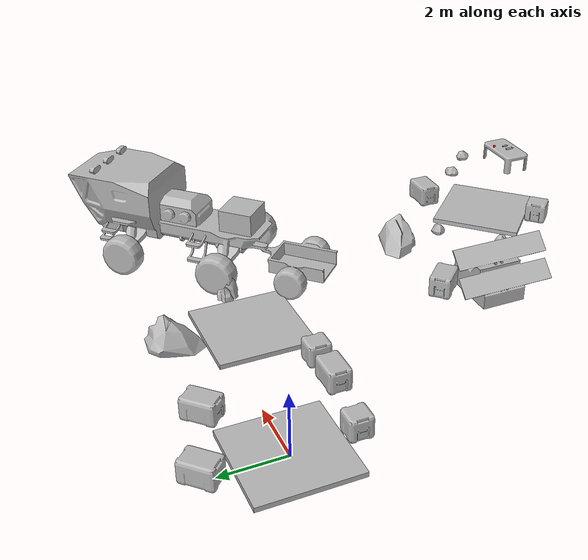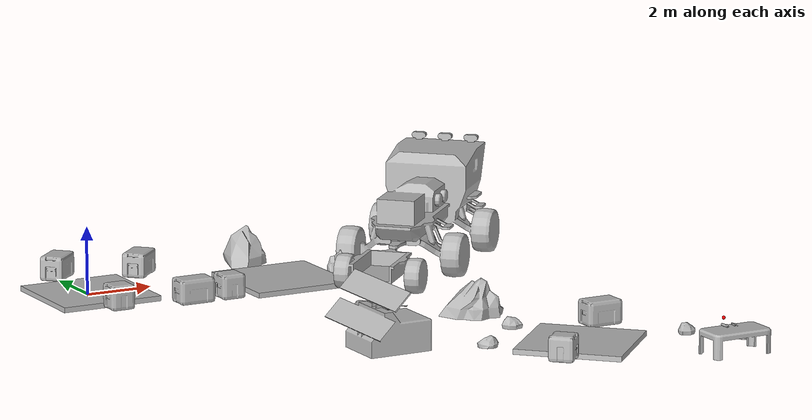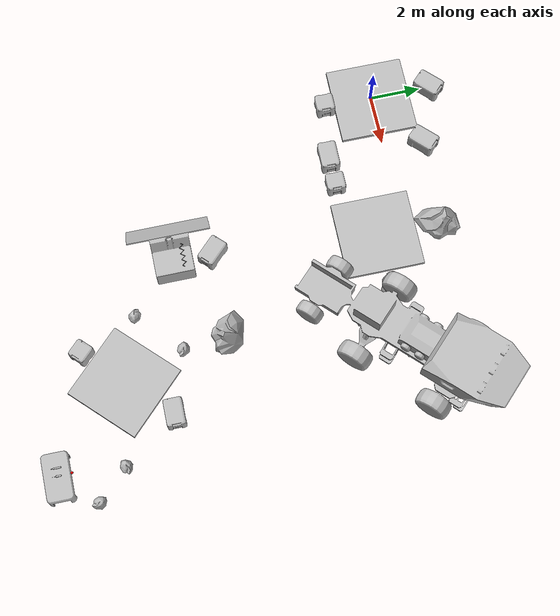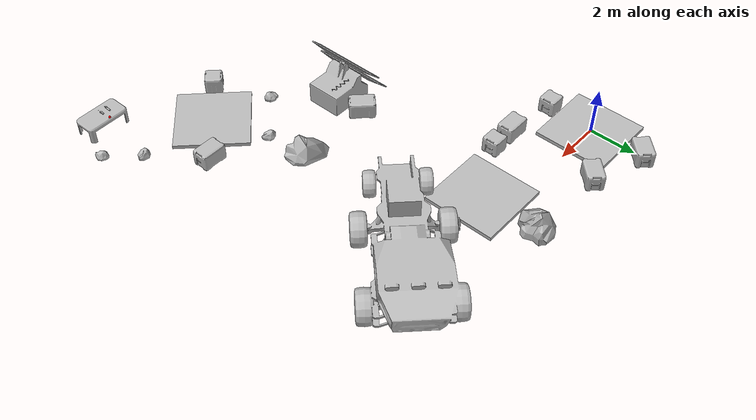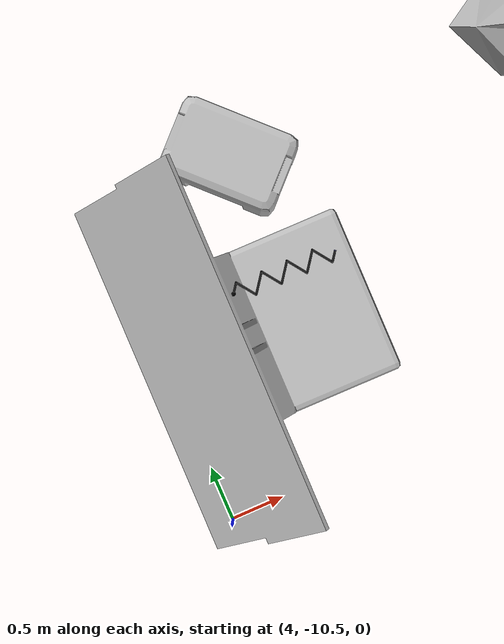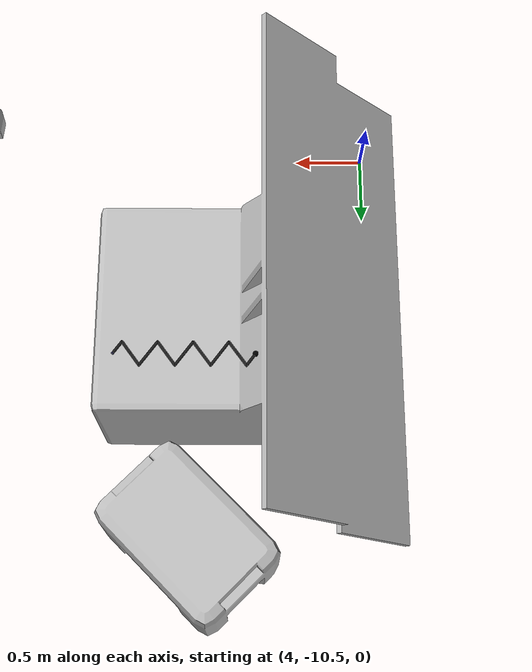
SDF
<sdf version="1.6">
 <world name="SRC_finals">
  <physics type="ode">
   <real_time_update_rate>1000.0</real_time_update_rate>
   <max_step_size>0.001</max_step_size>
   <real_time_factor>1</real_time_factor>
   <ode>
    <solver>
     <type>quick</type>
     <iters>150</iters>
     <precon_iters>0</precon_iters>
     <sor>1.400000</sor>
     <use_dynamic_moi_rescaling>1</use_dynamic_moi_rescaling>
    </solver>
    <constraints>
     <cfm>0.000000</cfm>
     <erp>0.800000</erp>
     <contact_max_correcting_vel>2000.000000</contact_max_correcting_vel>
     <contact_surface_layer>0.01000</contact_surface_layer>
    </constraints>
   </ode>
  </physics>
  <scene>
   <background>0.968627451 0.690196078 0.384313725 1.0</background>
   <grid>0</grid>
   <origin_visual>0</origin_visual>
  </scene>
  <light type="directional" name="sun">
   <pose>0 0 1000 -0.1700415195883993 -1.1783325251044838 0</pose>
   <diffuse>0.8 0.8 0.8 1</diffuse>
   <specular>0.2 0.2 0.2 1</specular>
   <attenuation>
    <range>1000</range>
    <constant>0.9</constant>
    <linear>0.01</linear>
    <quadratic>0.001</quadratic>
   </attenuation>
   <direction>-0.5 0.1 -0.9</direction>
  </light>
  <include>
   <name>walkway_1</name>
   <pose>0.09
      0
      -0.052151
      0
      0
      3.141592653589793</pose>
   <uri>model://walkway_finish_opposite</uri>
  </include>
  <include>
   <name>mars_crate_long_1</name>
   <pose>0.09000000000000037
      2.324
      0
      0
      0
      0.785398163397448</pose>
   <uri>model://mars_crate_long</uri>
  </include>
  <include>
   <name>mars_crate_2</name>
   <pose>0.08999999999999976
      -1.924
      0
      0
      0
      3.141592653589793</pose>
   <uri>model://mars_crate</uri>
  </include>
  <plugin name="boxT1Start" filename="libBoxContainsPlugin.so">
   <entity>valkyrie</entity>
   <namespace>task1/start</namespace>
   <pose>2.114
        -2.784846821261081e-16
        2.5
        0
        0
        -1.5707963267948968</pose>
   <size>1.524 1 5.0</size>
  </plugin>
  <plugin name="boxT1CP1" filename="libBoxContainsPlugin.so">
   <entity>valkyrie</entity>
   <namespace>task1/checkpoint1</namespace>
   <pose>2.687517287525381
        0.3267572875253808
        2.5
        0
        0
        0.7853981633974481</pose>
   <size>1 1 5.0</size>
  </plugin>
  <include>
   <name>mars_crate_long_3</name>
   <pose>2.3760000000000003
      1.5619999999999998
      0
      0
      0
      0.785398163397448</pose>
   <uri>model://mars_crate_long</uri>
  </include>
  <include>
   <name>mars_crate_4</name>
   <pose>3.4539547922204332
      -2.2397649636193724
      0
      0
      0
      3.141592653589793</pose>
   <uri>model://mars_crate</uri>
  </include>
  <include>
   <name>mars_crate_long_5</name>
   <pose>2.293909367271195
      -2.25305038856861
      0
      0
      0
      3.141592653589793</pose>
   <uri>model://mars_crate_long</uri>
  </include>
  <include>
   <name>walkway_4</name>
   <pose>5.739954792220433
      -1.0777649636193727
      -0.052151
      0
      0
      3.141592653589793</pose>
   <uri>model://walkway_finish_adjacent</uri>
  </include>
  <plugin name="boxT1CP3" filename="libBoxContainsPlugin.so">
   <entity>valkyrie</entity>
   <namespace>task1/checkpoint3</namespace>
   <pose>5.739954792220433
        -1.0777649636193727
        2.5
        0
        0
        3.141592653589793</pose>
   <size>3.048 3.048 5.0</size>
  </plugin>
  <include>
   <name>mars_rock_2_6</name>
   <pose>7.763954792220433
      -1.0777649636193727
      0
      0
      0
      -1.5707963267948968</pose>
   <uri>model://mars_rock_2</uri>
  </include>
  <include>
   <name>mars_rock_3_7</name>
   <pose>5.739954792220433
      1.5462350363806274
      0
      0
      0
      -1.8369701987210297e-16</pose>
   <uri>model://mars_rock_3</uri>
  </include>
  <plugin name="boxT2Start" filename="libBoxContainsPlugin.so">
   <entity>valkyrie</entity>
   <namespace>task2/start</namespace>
   <pose>5.739954792220433
        -3.101764963619373
        2.5
        0
        0
        3.141592653589793</pose>
   <size>1.524 1 5.0</size>
  </plugin>
  <include>
   <pose>10.539036134088196
        -0.7205184482799094
        0
        0
        0
        2.356194490192345</pose>
   <uri>model://mars_explorer</uri>
  </include>
  <include>
   <name>mars_crate_long_8</name>
   <pose>5.255719755839805
      -7.489719755839806
      0
      0
      0
      2.356194490192345</pose>
   <uri>model://mars_crate_long</uri>
  </include>
  <include>
   <name>mars_rock_3_9</name>
   <pose>8.679719755839805
      -7.489719755839806
      0
      0
      0
      -1.5707963267948968</pose>
   <uri>model://mars_rock_3</uri>
  </include>
  <include>
   <pose>5.417046200298301
        -9.02441469592094
        0
        0
        0
        1.5707963267948966</pose>
   <uri>model://solar_array</uri>
  </include>
  <model name="solar_panel_cable">
   <self_collide>true</self_collide>
   <pose>4.8170462002983
    -8.62441469592094
    0.85
    0
    0
    6.123233995736766e-17</pose>
   <link name="link_0">
    <inertial><mass>0.05</mass><inertia><ixx>0.0001</ixx><iyy>0.0001</iyy><izz>0.0001</izz></inertia></inertial>
    <visual name="visual">
     <geometry><sphere><radius>0.02</radius></sphere></geometry>
     <material>
      <ambient>0 0 0 1</ambient>
      <emissive>0 0 0 1</emissive>
      <diffuse>0 0 0 1</diffuse>
      <specular>1 1 1 1</specular>
     </material>
    </visual>
   </link>
   <link name="link_1">
    <pose>0.0 0 0 0 1.5707963267948966 0.9424777960769379</pose>
    <inertial>
     <pose>0 0 0.05 0 0 0</pose>
     <mass>0.05</mass>
     <inertia><ixx>0.0001</ixx><iyy>0.0001</iyy><izz>0.0001</izz></inertia>
    </inertial>
    <collision name="cylinder">
     <pose>0 0 0.05 0 0 0</pose>
     <geometry><cylinder><length>0.1</length><radius>0.01</radius></cylinder></geometry>
     <surface>
      <contact><ode><kp>1e5</kp><kd>1</kd><max_vel>0.1</max_vel><min_depth>0.0015</min_depth></ode></contact>
      <friction><ode><mu>1.0</mu><mu2>1.0</mu2></ode></friction>
     </surface>
    </collision>
    <collision name="sphere">
     <geometry><sphere><radius>0.01</radius></sphere></geometry>
     <surface>
      <contact><ode><kp>1e5</kp><kd>1</kd><max_vel>0.1</max_vel><min_depth>0.0015</min_depth></ode></contact>
      <friction><ode><mu>1.0</mu><mu2>1.0</mu2></ode></friction>
     </surface>
    </collision>
    <visual name="cylinder">
     <pose>0 0 0.05 0 0 0</pose>
     <geometry><cylinder><length>0.1</length><radius>0.01</radius></cylinder></geometry>
     <material>
      <ambient>0 0 0 1</ambient>
      <emissive>0 0 0 1</emissive>
      <diffuse>0.1 0.1 0.1 1</diffuse>
      <specular>1 1 1 1</specular>
     </material>
    </visual>
    <visual name="sphere">
     <geometry><sphere><radius>0.01</radius></sphere></geometry>
     <material>
      <ambient>0 0 0 1</ambient>
      <emissive>0 0 0 1</emissive>
      <diffuse>0.1 0.1 0.1 1</diffuse>
      <specular>1 1 1 1</specular>
     </material>
    </visual>
   </link>
   <joint name="joint_1" type="universal">
    <child>link_1</child>
    <parent>link_0</parent>
    <axis>
     <xyz>0 1 0</xyz>
     <limit><lower>-1.5707963267948966</lower><upper>1.5707963267948966</upper></limit>
    </axis>
    <axis2>
     <xyz>-1 0 0</xyz>
     <limit><lower>-1.5707963267948966</lower><upper>1.5707963267948966</upper></limit>
    </axis2>
    <physics><ode><cfm_damping>1</cfm_damping></ode></physics>
   </joint>
   <link name="link_2">
    <pose>0.058778525229247314 0.08090169943749476 0 0 1.5707963267948966 -0.9424777960769379</pose>
    <inertial>
     <pose>0 0 0.05 0 0 0</pose>
     <mass>0.05</mass>
     <inertia><ixx>0.0001</ixx><iyy>0.0001</iyy><izz>0.0001</izz></inertia>
    </inertial>
    <collision name="cylinder">
     <pose>0 0 0.05 0 0 0</pose>
     <geometry><cylinder><length>0.1</length><radius>0.01</radius></cylinder></geometry>
     <surface>
      <contact><ode><kp>1e5</kp><kd>1</kd><max_vel>0.1</max_vel><min_depth>0.0015</min_depth></ode></contact>
      <friction><ode><mu>1.0</mu><mu2>1.0</mu2></ode></friction>
     </surface>
    </collision>
    <collision name="sphere">
     <geometry><sphere><radius>0.01</radius></sphere></geometry>
     <surface>
      <contact><ode><kp>1e5</kp><kd>1</kd><max_vel>0.1</max_vel><min_depth>0.0015</min_depth></ode></contact>
      <friction><ode><mu>1.0</mu><mu2>1.0</mu2></ode></friction>
     </surface>
    </collision>
    <visual name="cylinder">
     <pose>0 0 0.05 0 0 0</pose>
     <geometry><cylinder><length>0.1</length><radius>0.01</radius></cylinder></geometry>
     <material>
      <ambient>0 0 0 1</ambient>
      <emissive>0 0 0 1</emissive>
      <diffuse>0.1 0.1 0.1 1</diffuse>
      <specular>1 1 1 1</specular>
     </material>
    </visual>
    <visual name="sphere">
     <geometry><sphere><radius>0.01</radius></sphere></geometry>
     <material>
      <ambient>0 0 0 1</ambient>
      <emissive>0 0 0 1</emissive>
      <diffuse>0.1 0.1 0.1 1</diffuse>
      <specular>1 1 1 1</specular>
     </material>
    </visual>
   </link>
   <joint name="joint_2" type="universal">
    <child>link_2</child>
    <parent>link_1</parent>
    <axis>
     <xyz>0 1 0</xyz>
     <limit><lower>-1.5707963267948966</lower><upper>1.5707963267948966</upper></limit>
    </axis>
    <axis2>
     <xyz>-1 0 0</xyz>
     <limit><lower>-1.5707963267948966</lower><upper>1.5707963267948966</upper></limit>
    </axis2>
    <physics><ode><cfm_damping>1</cfm_damping></ode></physics>
   </joint>
   <link name="link_3">
    <pose>0.11755705045849463 0 0 0 1.5707963267948966 -0.9424777960769379</pose>
    <inertial>
     <pose>0 0 0.05 0 0 0</pose>
     <mass>0.05</mass>
     <inertia><ixx>0.0001</ixx><iyy>0.0001</iyy><izz>0.0001</izz></inertia>
    </inertial>
    <collision name="cylinder">
     <pose>0 0 0.05 0 0 0</pose>
     <geometry><cylinder><length>0.1</length><radius>0.01</radius></cylinder></geometry>
     <surface>
      <contact><ode><kp>1e5</kp><kd>1</kd><max_vel>0.1</max_vel><min_depth>0.0015</min_depth></ode></contact>
      <friction><ode><mu>1.0</mu><mu2>1.0</mu2></ode></friction>
     </surface>
    </collision>
    <collision name="sphere">
     <geometry><sphere><radius>0.01</radius></sphere></geometry>
     <surface>
      <contact><ode><kp>1e5</kp><kd>1</kd><max_vel>0.1</max_vel><min_depth>0.0015</min_depth></ode></contact>
      <friction><ode><mu>1.0</mu><mu2>1.0</mu2></ode></friction>
     </surface>
    </collision>
    <visual name="cylinder">
     <pose>0 0 0.05 0 0 0</pose>
     <geometry><cylinder><length>0.1</length><radius>0.01</radius></cylinder></geometry>
     <material>
      <ambient>0 0 0 1</ambient>
      <emissive>0 0 0 1</emissive>
      <diffuse>0.1 0.1 0.1 1</diffuse>
      <specular>1 1 1 1</specular>
     </material>
    </visual>
    <visual name="sphere">
     <geometry><sphere><radius>0.01</radius></sphere></geometry>
     <material>
      <ambient>0 0 0 1</ambient>
      <emissive>0 0 0 1</emissive>
      <diffuse>0.1 0.1 0.1 1</diffuse>
      <specular>1 1 1 1</specular>
     </material>
    </visual>
   </link>
   <joint name="joint_3" type="universal">
    <child>link_3</child>
    <parent>link_2</parent>
    <axis>
     <xyz>0 1 0</xyz>
     <limit><lower>-1.5707963267948966</lower><upper>1.5707963267948966</upper></limit>
    </axis>
    <axis2>
     <xyz>-1 0 0</xyz>
     <limit><lower>-1.5707963267948966</lower><upper>1.5707963267948966</upper></limit>
    </axis2>
    <physics><ode><cfm_damping>1</cfm_damping></ode></physics>
   </joint>
   <link name="link_4">
    <pose>0.17633557568774197 -0.08090169943749476 0 0 1.5707963267948966 0.9424777960769379</pose>
    <inertial>
     <pose>0 0 0.05 0 0 0</pose>
     <mass>0.05</mass>
     <inertia><ixx>0.0001</ixx><iyy>0.0001</iyy><izz>0.0001</izz></inertia>
    </inertial>
    <collision name="cylinder">
     <pose>0 0 0.05 0 0 0</pose>
     <geometry><cylinder><length>0.1</length><radius>0.01</radius></cylinder></geometry>
     <surface>
      <contact><ode><kp>1e5</kp><kd>1</kd><max_vel>0.1</max_vel><min_depth>0.0015</min_depth></ode></contact>
      <friction><ode><mu>1.0</mu><mu2>1.0</mu2></ode></friction>
     </surface>
    </collision>
    <collision name="sphere">
     <geometry><sphere><radius>0.01</radius></sphere></geometry>
     <surface>
      <contact><ode><kp>1e5</kp><kd>1</kd><max_vel>0.1</max_vel><min_depth>0.0015</min_depth></ode></contact>
      <friction><ode><mu>1.0</mu><mu2>1.0</mu2></ode></friction>
     </surface>
    </collision>
    <visual name="cylinder">
     <pose>0 0 0.05 0 0 0</pose>
     <geometry><cylinder><length>0.1</length><radius>0.01</radius></cylinder></geometry>
     <material>
      <ambient>0 0 0 1</ambient>
      <emissive>0 0 0 1</emissive>
      <diffuse>0.1 0.1 0.1 1</diffuse>
      <specular>1 1 1 1</specular>
     </material>
    </visual>
    <visual name="sphere">
     <geometry><sphere><radius>0.01</radius></sphere></geometry>
     <material>
      <ambient>0 0 0 1</ambient>
      <emissive>0 0 0 1</emissive>
      <diffuse>0.1 0.1 0.1 1</diffuse>
      <specular>1 1 1 1</specular>
     </material>
    </visual>
   </link>
   <joint name="joint_4" type="universal">
    <child>link_4</child>
    <parent>link_3</parent>
    <axis>
     <xyz>0 1 0</xyz>
     <limit><lower>-1.5707963267948966</lower><upper>1.5707963267948966</upper></limit>
    </axis>
    <axis2>
     <xyz>-1 0 0</xyz>
     <limit><lower>-1.5707963267948966</lower><upper>1.5707963267948966</upper></limit>
    </axis2>
    <physics><ode><cfm_damping>1</cfm_damping></ode></physics>
   </joint>
   <link name="link_5">
    <pose>0.23511410091698925 0 0 0 1.5707963267948966 0.9424777960769379</pose>
    <inertial>
     <pose>0 0 0.05 0 0 0</pose>
     <mass>0.05</mass>
     <inertia><ixx>0.0001</ixx><iyy>0.0001</iyy><izz>0.0001</izz></inertia>
    </inertial>
    <collision name="cylinder">
     <pose>0 0 0.05 0 0 0</pose>
     <geometry><cylinder><length>0.1</length><radius>0.01</radius></cylinder></geometry>
     <surface>
      <contact><ode><kp>1e5</kp><kd>1</kd><max_vel>0.1</max_vel><min_depth>0.0015</min_depth></ode></contact>
      <friction><ode><mu>1.0</mu><mu2>1.0</mu2></ode></friction>
     </surface>
    </collision>
    <collision name="sphere">
     <geometry><sphere><radius>0.01</radius></sphere></geometry>
     <surface>
      <contact><ode><kp>1e5</kp><kd>1</kd><max_vel>0.1</max_vel><min_depth>0.0015</min_depth></ode></contact>
      <friction><ode><mu>1.0</mu><mu2>1.0</mu2></ode></friction>
     </surface>
    </collision>
    <visual name="cylinder">
     <pose>0 0 0.05 0 0 0</pose>
     <geometry><cylinder><length>0.1</length><radius>0.01</radius></cylinder></geometry>
     <material>
      <ambient>0 0 0 1</ambient>
      <emissive>0 0 0 1</emissive>
      <diffuse>0.1 0.1 0.1 1</diffuse>
      <specular>1 1 1 1</specular>
     </material>
    </visual>
    <visual name="sphere">
     <geometry><sphere><radius>0.01</radius></sphere></geometry>
     <material>
      <ambient>0 0 0 1</ambient>
      <emissive>0 0 0 1</emissive>
      <diffuse>0.1 0.1 0.1 1</diffuse>
      <specular>1 1 1 1</specular>
     </material>
    </visual>
   </link>
   <joint name="joint_5" type="universal">
    <child>link_5</child>
    <parent>link_4</parent>
    <axis>
     <xyz>0 1 0</xyz>
     <limit><lower>-1.5707963267948966</lower><upper>1.5707963267948966</upper></limit>
    </axis>
    <axis2>
     <xyz>-1 0 0</xyz>
     <limit><lower>-1.5707963267948966</lower><upper>1.5707963267948966</upper></limit>
    </axis2>
    <physics><ode><cfm_damping>1</cfm_damping></ode></physics>
   </joint>
   <link name="link_6">
    <pose>0.29389262614623657 0.08090169943749476 0 0 1.5707963267948966 -0.9424777960769379</pose>
    <inertial>
     <pose>0 0 0.05 0 0 0</pose>
     <mass>0.05</mass>
     <inertia><ixx>0.0001</ixx><iyy>0.0001</iyy><izz>0.0001</izz></inertia>
    </inertial>
    <collision name="cylinder">
     <pose>0 0 0.05 0 0 0</pose>
     <geometry><cylinder><length>0.1</length><radius>0.01</radius></cylinder></geometry>
     <surface>
      <contact><ode><kp>1e5</kp><kd>1</kd><max_vel>0.1</max_vel><min_depth>0.0015</min_depth></ode></contact>
      <friction><ode><mu>1.0</mu><mu2>1.0</mu2></ode></friction>
     </surface>
    </collision>
    <collision name="sphere">
     <geometry><sphere><radius>0.01</radius></sphere></geometry>
     <surface>
      <contact><ode><kp>1e5</kp><kd>1</kd><max_vel>0.1</max_vel><min_depth>0.0015</min_depth></ode></contact>
      <friction><ode><mu>1.0</mu><mu2>1.0</mu2></ode></friction>
     </surface>
    </collision>
    <visual name="cylinder">
     <pose>0 0 0.05 0 0 0</pose>
     <geometry><cylinder><length>0.1</length><radius>0.01</radius></cylinder></geometry>
     <material>
      <ambient>0 0 0 1</ambient>
      <emissive>0 0 0 1</emissive>
      <diffuse>0.1 0.1 0.1 1</diffuse>
      <specular>1 1 1 1</specular>
     </material>
    </visual>
    <visual name="sphere">
     <geometry><sphere><radius>0.01</radius></sphere></geometry>
     <material>
      <ambient>0 0 0 1</ambient>
      <emissive>0 0 0 1</emissive>
      <diffuse>0.1 0.1 0.1 1</diffuse>
      <specular>1 1 1 1</specular>
     </material>
    </visual>
   </link>
   <joint name="joint_6" type="universal">
    <child>link_6</child>
    <parent>link_5</parent>
    <axis>
     <xyz>0 1 0</xyz>
     <limit><lower>-1.5707963267948966</lower><upper>1.5707963267948966</upper></limit>
    </axis>
    <axis2>
     <xyz>-1 0 0</xyz>
     <limit><lower>-1.5707963267948966</lower><upper>1.5707963267948966</upper></limit>
    </axis2>
    <physics><ode><cfm_damping>1</cfm_damping></ode></physics>
   </joint>
   <link name="link_7">
    <pose>0.35267115137548394 0 0 0 1.5707963267948966 -0.9424777960769379</pose>
    <inertial>
     <pose>0 0 0.05 0 0 0</pose>
     <mass>0.05</mass>
     <inertia><ixx>0.0001</ixx><iyy>0.0001</iyy><izz>0.0001</izz></inertia>
    </inertial>
    <collision name="cylinder">
     <pose>0 0 0.05 0 0 0</pose>
     <geometry><cylinder><length>0.1</length><radius>0.01</radius></cylinder></geometry>
     <surface>
      <contact><ode><kp>1e5</kp><kd>1</kd><max_vel>0.1</max_vel><min_depth>0.0015</min_depth></ode></contact>
      <friction><ode><mu>1.0</mu><mu2>1.0</mu2></ode></friction>
     </surface>
    </collision>
    <collision name="sphere">
     <geometry><sphere><radius>0.01</radius></sphere></geometry>
     <surface>
      <contact><ode><kp>1e5</kp><kd>1</kd><max_vel>0.1</max_vel><min_depth>0.0015</min_depth></ode></contact>
      <friction><ode><mu>1.0</mu><mu2>1.0</mu2></ode></friction>
     </surface>
    </collision>
    <visual name="cylinder">
     <pose>0 0 0.05 0 0 0</pose>
     <geometry><cylinder><length>0.1</length><radius>0.01</radius></cylinder></geometry>
     <material>
      <ambient>0 0 0 1</ambient>
      <emissive>0 0 0 1</emissive>
      <diffuse>0.1 0.1 0.1 1</diffuse>
      <specular>1 1 1 1</specular>
     </material>
    </visual>
    <visual name="sphere">
     <geometry><sphere><radius>0.01</radius></sphere></geometry>
     <material>
      <ambient>0 0 0 1</ambient>
      <emissive>0 0 0 1</emissive>
      <diffuse>0.1 0.1 0.1 1</diffuse>
      <specular>1 1 1 1</specular>
     </material>
    </visual>
   </link>
   <joint name="joint_7" type="universal">
    <child>link_7</child>
    <parent>link_6</parent>
    <axis>
     <xyz>0 1 0</xyz>
     <limit><lower>-1.5707963267948966</lower><upper>1.5707963267948966</upper></limit>
    </axis>
    <axis2>
     <xyz>-1 0 0</xyz>
     <limit><lower>-1.5707963267948966</lower><upper>1.5707963267948966</upper></limit>
    </axis2>
    <physics><ode><cfm_damping>1</cfm_damping></ode></physics>
   </joint>
   <link name="link_8">
    <pose>0.41144967660473125 -0.08090169943749476 0 0 1.5707963267948966 0.9424777960769379</pose>
    <inertial>
     <pose>0 0 0.05 0 0 0</pose>
     <mass>0.05</mass>
     <inertia><ixx>0.0001</ixx><iyy>0.0001</iyy><izz>0.0001</izz></inertia>
    </inertial>
    <collision name="cylinder">
     <pose>0 0 0.05 0 0 0</pose>
     <geometry><cylinder><length>0.1</length><radius>0.01</radius></cylinder></geometry>
     <surface>
      <contact><ode><kp>1e5</kp><kd>1</kd><max_vel>0.1</max_vel><min_depth>0.0015</min_depth></ode></contact>
      <friction><ode><mu>1.0</mu><mu2>1.0</mu2></ode></friction>
     </surface>
    </collision>
    <collision name="sphere">
     <geometry><sphere><radius>0.01</radius></sphere></geometry>
     <surface>
      <contact><ode><kp>1e5</kp><kd>1</kd><max_vel>0.1</max_vel><min_depth>0.0015</min_depth></ode></contact>
      <friction><ode><mu>1.0</mu><mu2>1.0</mu2></ode></friction>
     </surface>
    </collision>
    <visual name="cylinder">
     <pose>0 0 0.05 0 0 0</pose>
     <geometry><cylinder><length>0.1</length><radius>0.01</radius></cylinder></geometry>
     <material>
      <ambient>0 0 0 1</ambient>
      <emissive>0 0 0 1</emissive>
      <diffuse>0.1 0.1 0.1 1</diffuse>
      <specular>1 1 1 1</specular>
     </material>
    </visual>
    <visual name="sphere">
     <geometry><sphere><radius>0.01</radius></sphere></geometry>
     <material>
      <ambient>0 0 0 1</ambient>
      <emissive>0 0 0 1</emissive>
      <diffuse>0.1 0.1 0.1 1</diffuse>
      <specular>1 1 1 1</specular>
     </material>
    </visual>
   </link>
   <joint name="joint_8" type="universal">
    <child>link_8</child>
    <parent>link_7</parent>
    <axis>
     <xyz>0 1 0</xyz>
     <limit><lower>-1.5707963267948966</lower><upper>1.5707963267948966</upper></limit>
    </axis>
    <axis2>
     <xyz>-1 0 0</xyz>
     <limit><lower>-1.5707963267948966</lower><upper>1.5707963267948966</upper></limit>
    </axis2>
    <physics><ode><cfm_damping>1</cfm_damping></ode></physics>
   </joint>
   <link name="link_9">
    <pose>0.4702282018339785 0 0 0 1.5707963267948966 0.9424777960769379</pose>
    <inertial>
     <pose>0 0 0.05 0 0 0</pose>
     <mass>0.05</mass>
     <inertia><ixx>0.0001</ixx><iyy>0.0001</iyy><izz>0.0001</izz></inertia>
    </inertial>
    <collision name="cylinder">
     <pose>0 0 0.05 0 0 0</pose>
     <geometry><cylinder><length>0.1</length><radius>0.01</radius></cylinder></geometry>
     <surface>
      <contact><ode><kp>1e5</kp><kd>1</kd><max_vel>0.1</max_vel><min_depth>0.0015</min_depth></ode></contact>
      <friction><ode><mu>1.0</mu><mu2>1.0</mu2></ode></friction>
     </surface>
    </collision>
    <collision name="sphere">
     <geometry><sphere><radius>0.01</radius></sphere></geometry>
     <surface>
      <contact><ode><kp>1e5</kp><kd>1</kd><max_vel>0.1</max_vel><min_depth>0.0015</min_depth></ode></contact>
      <friction><ode><mu>1.0</mu><mu2>1.0</mu2></ode></friction>
     </surface>
    </collision>
    <visual name="cylinder">
     <pose>0 0 0.05 0 0 0</pose>
     <geometry><cylinder><length>0.1</length><radius>0.01</radius></cylinder></geometry>
     <material>
      <ambient>0 0 0 1</ambient>
      <emissive>0 0 0 1</emissive>
      <diffuse>0.1 0.1 0.1 1</diffuse>
      <specular>1 1 1 1</specular>
     </material>
    </visual>
    <visual name="sphere">
     <geometry><sphere><radius>0.01</radius></sphere></geometry>
     <material>
      <ambient>0 0 0 1</ambient>
      <emissive>0 0 0 1</emissive>
      <diffuse>0.1 0.1 0.1 1</diffuse>
      <specular>1 1 1 1</specular>
     </material>
    </visual>
   </link>
   <joint name="joint_9" type="universal">
    <child>link_9</child>
    <parent>link_8</parent>
    <axis>
     <xyz>0 1 0</xyz>
     <limit><lower>-1.5707963267948966</lower><upper>1.5707963267948966</upper></limit>
    </axis>
    <axis2>
     <xyz>-1 0 0</xyz>
     <limit><lower>-1.5707963267948966</lower><upper>1.5707963267948966</upper></limit>
    </axis2>
    <physics><ode><cfm_damping>1</cfm_damping></ode></physics>
   </joint>
   <link name="link_10">
    <pose>0.5290067270632258 0.08090169943749476 0 0 1.5707963267948966 -0.9424777960769379</pose>
    <inertial>
     <pose>0 0 0.05 0 0 0</pose>
     <mass>0.05</mass>
     <inertia><ixx>0.0001</ixx><iyy>0.0001</iyy><izz>0.0001</izz></inertia>
    </inertial>
    <collision name="cylinder">
     <pose>0 0 0.05 0 0 0</pose>
     <geometry><cylinder><length>0.1</length><radius>0.01</radius></cylinder></geometry>
     <surface>
      <contact><ode><kp>1e5</kp><kd>1</kd><max_vel>0.1</max_vel><min_depth>0.0015</min_depth></ode></contact>
      <friction><ode><mu>1.0</mu><mu2>1.0</mu2></ode></friction>
     </surface>
    </collision>
    <collision name="sphere">
     <geometry><sphere><radius>0.01</radius></sphere></geometry>
     <surface>
      <contact><ode><kp>1e5</kp><kd>1</kd><max_vel>0.1</max_vel><min_depth>0.0015</min_depth></ode></contact>
      <friction><ode><mu>1.0</mu><mu2>1.0</mu2></ode></friction>
     </surface>
    </collision>
    <visual name="cylinder">
     <pose>0 0 0.05 0 0 0</pose>
     <geometry><cylinder><length>0.1</length><radius>0.01</radius></cylinder></geometry>
     <material>
      <ambient>0 0 0 1</ambient>
      <emissive>0 0 0 1</emissive>
      <diffuse>0.1 0.1 0.1 1</diffuse>
      <specular>1 1 1 1</specular>
     </material>
    </visual>
    <visual name="sphere">
     <geometry><sphere><radius>0.01</radius></sphere></geometry>
     <material>
      <ambient>0 0 0 1</ambient>
      <emissive>0 0 0 1</emissive>
      <diffuse>0.1 0.1 0.1 1</diffuse>
      <specular>1 1 1 1</specular>
     </material>
    </visual>
   </link>
   <joint name="joint_10" type="universal">
    <child>link_10</child>
    <parent>link_9</parent>
    <axis>
     <xyz>0 1 0</xyz>
     <limit><lower>-1.5707963267948966</lower><upper>1.5707963267948966</upper></limit>
    </axis>
    <axis2>
     <xyz>-1 0 0</xyz>
     <limit><lower>-1.5707963267948966</lower><upper>1.5707963267948966</upper></limit>
    </axis2>
    <physics><ode><cfm_damping>1</cfm_damping></ode></physics>
   </joint>
   <link name="link_11">
    <pose>0.5877852522924731 0 0 0 1.5707963267948966 -0.9424777960769379</pose>
    <inertial>
     <pose>0 0 0.05 0 0 0</pose>
     <mass>0.05</mass>
     <inertia><ixx>0.0001</ixx><iyy>0.0001</iyy><izz>0.0001</izz></inertia>
    </inertial>
    <collision name="cylinder">
     <pose>0 0 0.05 0 0 0</pose>
     <geometry><cylinder><length>0.1</length><radius>0.01</radius></cylinder></geometry>
     <surface>
      <contact><ode><kp>1e5</kp><kd>1</kd><max_vel>0.1</max_vel><min_depth>0.0015</min_depth></ode></contact>
      <friction><ode><mu>1.0</mu><mu2>1.0</mu2></ode></friction>
     </surface>
    </collision>
    <collision name="sphere">
     <geometry><sphere><radius>0.01</radius></sphere></geometry>
     <surface>
      <contact><ode><kp>1e5</kp><kd>1</kd><max_vel>0.1</max_vel><min_depth>0.0015</min_depth></ode></contact>
      <friction><ode><mu>1.0</mu><mu2>1.0</mu2></ode></friction>
     </surface>
    </collision>
    <visual name="cylinder">
     <pose>0 0 0.05 0 0 0</pose>
     <geometry><cylinder><length>0.1</length><radius>0.01</radius></cylinder></geometry>
     <material>
      <ambient>0 0 0 1</ambient>
      <emissive>0 0 0 1</emissive>
      <diffuse>0.1 0.1 0.1 1</diffuse>
      <specular>1 1 1 1</specular>
     </material>
    </visual>
    <visual name="sphere">
     <geometry><sphere><radius>0.01</radius></sphere></geometry>
     <material>
      <ambient>0 0 0 1</ambient>
      <emissive>0 0 0 1</emissive>
      <diffuse>0.1 0.1 0.1 1</diffuse>
      <specular>1 1 1 1</specular>
     </material>
    </visual>
   </link>
   <joint name="joint_11" type="universal">
    <child>link_11</child>
    <parent>link_10</parent>
    <axis>
     <xyz>0 1 0</xyz>
     <limit><lower>-1.5707963267948966</lower><upper>1.5707963267948966</upper></limit>
    </axis>
    <axis2>
     <xyz>-1 0 0</xyz>
     <limit><lower>-1.5707963267948966</lower><upper>1.5707963267948966</upper></limit>
    </axis2>
    <physics><ode><cfm_damping>1</cfm_damping></ode></physics>
   </joint>
   <link name="link_12">
    <pose>0.6465637775217205 -0.08090169943749476 0 0 1.5707963267948966 0.9424777960769379</pose>
    <inertial>
     <pose>0 0 0.05 0 0 0</pose>
     <mass>0.05</mass>
     <inertia><ixx>0.0001</ixx><iyy>0.0001</iyy><izz>0.0001</izz></inertia>
    </inertial>
    <collision name="cylinder">
     <pose>0 0 0.05 0 0 0</pose>
     <geometry><cylinder><length>0.1</length><radius>0.01</radius></cylinder></geometry>
     <surface>
      <contact><ode><kp>1e5</kp><kd>1</kd><max_vel>0.1</max_vel><min_depth>0.0015</min_depth></ode></contact>
      <friction><ode><mu>1.0</mu><mu2>1.0</mu2></ode></friction>
     </surface>
    </collision>
    <collision name="sphere">
     <geometry><sphere><radius>0.01</radius></sphere></geometry>
     <surface>
      <contact><ode><kp>1e5</kp><kd>1</kd><max_vel>0.1</max_vel><min_depth>0.0015</min_depth></ode></contact>
      <friction><ode><mu>1.0</mu><mu2>1.0</mu2></ode></friction>
     </surface>
    </collision>
    <visual name="cylinder">
     <pose>0 0 0.05 0 0 0</pose>
     <geometry><cylinder><length>0.1</length><radius>0.01</radius></cylinder></geometry>
     <material>
      <ambient>0 0 0 1</ambient>
      <emissive>0 0 0 1</emissive>
      <diffuse>0.1 0.1 0.1 1</diffuse>
      <specular>1 1 1 1</specular>
     </material>
    </visual>
    <visual name="sphere">
     <geometry><sphere><radius>0.01</radius></sphere></geometry>
     <material>
      <ambient>0 0 0 1</ambient>
      <emissive>0 0 0 1</emissive>
      <diffuse>0.1 0.1 0.1 1</diffuse>
      <specular>1 1 1 1</specular>
     </material>
    </visual>
   </link>
   <joint name="joint_12" type="universal">
    <child>link_12</child>
    <parent>link_11</parent>
    <axis>
     <xyz>0 1 0</xyz>
     <limit><lower>-1.5707963267948966</lower><upper>1.5707963267948966</upper></limit>
    </axis>
    <axis2>
     <xyz>-1 0 0</xyz>
     <limit><lower>-1.5707963267948966</lower><upper>1.5707963267948966</upper></limit>
    </axis2>
    <physics><ode><cfm_damping>1</cfm_damping></ode></physics>
   </joint>
   <link name="link_13">
    <pose>0.7053423027509679 0 0 0 1.5707963267948966 0.9424777960769379</pose>
    <inertial>
     <pose>0 0 0.05 0 0 0</pose>
     <mass>0.05</mass>
     <inertia><ixx>0.0001</ixx><iyy>0.0001</iyy><izz>0.0001</izz></inertia>
    </inertial>
    <collision name="cylinder">
     <pose>0 0 0.05 0 0 0</pose>
     <geometry><cylinder><length>0.1</length><radius>0.01</radius></cylinder></geometry>
     <surface>
      <contact><ode><kp>1e5</kp><kd>1</kd><max_vel>0.1</max_vel><min_depth>0.0015</min_depth></ode></contact>
      <friction><ode><mu>1.0</mu><mu2>1.0</mu2></ode></friction>
     </surface>
    </collision>
    <collision name="sphere">
     <geometry><sphere><radius>0.01</radius></sphere></geometry>
     <surface>
      <contact><ode><kp>1e5</kp><kd>1</kd><max_vel>0.1</max_vel><min_depth>0.0015</min_depth></ode></contact>
      <friction><ode><mu>1.0</mu><mu2>1.0</mu2></ode></friction>
     </surface>
    </collision>
    <visual name="cylinder">
     <pose>0 0 0.05 0 0 0</pose>
     <geometry><cylinder><length>0.1</length><radius>0.01</radius></cylinder></geometry>
     <material>
      <ambient>0 0 0 1</ambient>
      <emissive>0 0 0 1</emissive>
      <diffuse>0.1 0.1 0.1 1</diffuse>
      <specular>1 1 1 1</specular>
     </material>
    </visual>
    <visual name="sphere">
     <geometry><sphere><radius>0.01</radius></sphere></geometry>
     <material>
      <ambient>0 0 0 1</ambient>
      <emissive>0 0 0 1</emissive>
      <diffuse>0.1 0.1 0.1 1</diffuse>
      <specular>1 1 1 1</specular>
     </material>
    </visual>
   </link>
   <joint name="joint_13" type="universal">
    <child>link_13</child>
    <parent>link_12</parent>
    <axis>
     <xyz>0 1 0</xyz>
     <limit><lower>-1.5707963267948966</lower><upper>1.5707963267948966</upper></limit>
    </axis>
    <axis2>
     <xyz>-1 0 0</xyz>
     <limit><lower>-1.5707963267948966</lower><upper>1.5707963267948966</upper></limit>
    </axis2>
    <physics><ode><cfm_damping>1</cfm_damping></ode></physics>
   </joint>
   <link name="link_14">
    <pose>0.7641208279802151 0.08090169943749476 0 0 1.5707963267948966 -0.9424777960769379</pose>
    <inertial>
     <pose>0 0 0.05 0 0 0</pose>
     <mass>0.05</mass>
     <inertia><ixx>0.0001</ixx><iyy>0.0001</iyy><izz>0.0001</izz></inertia>
    </inertial>
    <collision name="cylinder">
     <pose>0 0 0.05 0 0 0</pose>
     <geometry><cylinder><length>0.1</length><radius>0.01</radius></cylinder></geometry>
     <surface>
      <contact><ode><kp>1e5</kp><kd>1</kd><max_vel>0.1</max_vel><min_depth>0.0015</min_depth></ode></contact>
      <friction><ode><mu>1.0</mu><mu2>1.0</mu2></ode></friction>
     </surface>
    </collision>
    <collision name="sphere">
     <geometry><sphere><radius>0.01</radius></sphere></geometry>
     <surface>
      <contact><ode><kp>1e5</kp><kd>1</kd><max_vel>0.1</max_vel><min_depth>0.0015</min_depth></ode></contact>
      <friction><ode><mu>1.0</mu><mu2>1.0</mu2></ode></friction>
     </surface>
    </collision>
    <visual name="cylinder">
     <pose>0 0 0.05 0 0 0</pose>
     <geometry><cylinder><length>0.1</length><radius>0.01</radius></cylinder></geometry>
     <material>
      <ambient>0 0 0 1</ambient>
      <emissive>0 0 0 1</emissive>
      <diffuse>0.1 0.1 0.1 1</diffuse>
      <specular>1 1 1 1</specular>
     </material>
    </visual>
    <visual name="sphere">
     <geometry><sphere><radius>0.01</radius></sphere></geometry>
     <material>
      <ambient>0 0 0 1</ambient>
      <emissive>0 0 0 1</emissive>
      <diffuse>0.1 0.1 0.1 1</diffuse>
      <specular>1 1 1 1</specular>
     </material>
    </visual>
   </link>
   <joint name="joint_14" type="universal">
    <child>link_14</child>
    <parent>link_13</parent>
    <axis>
     <xyz>0 1 0</xyz>
     <limit><lower>-1.5707963267948966</lower><upper>1.5707963267948966</upper></limit>
    </axis>
    <axis2>
     <xyz>-1 0 0</xyz>
     <limit><lower>-1.5707963267948966</lower><upper>1.5707963267948966</upper></limit>
    </axis2>
    <physics><ode><cfm_damping>1</cfm_damping></ode></physics>
   </joint>
   <link name="link_15">
    <pose>0.8228993532094625 0 0 0 1.5707963267948966 -0.9424777960769379</pose>
    <inertial>
     <pose>0 0 0.05 0 0 0</pose>
     <mass>0.05</mass>
     <inertia><ixx>0.0001</ixx><iyy>0.0001</iyy><izz>0.0001</izz></inertia>
    </inertial>
    <collision name="cylinder">
     <pose>0 0 0.05 0 0 0</pose>
     <geometry><cylinder><length>0.1</length><radius>0.01</radius></cylinder></geometry>
     <surface>
      <contact><ode><kp>1e5</kp><kd>1</kd><max_vel>0.1</max_vel><min_depth>0.0015</min_depth></ode></contact>
      <friction><ode><mu>1.0</mu><mu2>1.0</mu2></ode></friction>
     </surface>
    </collision>
    <collision name="sphere">
     <geometry><sphere><radius>0.01</radius></sphere></geometry>
     <surface>
      <contact><ode><kp>1e5</kp><kd>1</kd><max_vel>0.1</max_vel><min_depth>0.0015</min_depth></ode></contact>
      <friction><ode><mu>1.0</mu><mu2>1.0</mu2></ode></friction>
     </surface>
    </collision>
    <visual name="cylinder">
     <pose>0 0 0.05 0 0 0</pose>
     <geometry><cylinder><length>0.1</length><radius>0.01</radius></cylinder></geometry>
     <material>
      <ambient>0 0 0 1</ambient>
      <emissive>0 0 0 1</emissive>
      <diffuse>0.1 0.1 0.1 1</diffuse>
      <specular>1 1 1 1</specular>
     </material>
    </visual>
    <visual name="sphere">
     <geometry><sphere><radius>0.01</radius></sphere></geometry>
     <material>
      <ambient>0 0 0 1</ambient>
      <emissive>0 0 0 1</emissive>
      <diffuse>0.1 0.1 0.1 1</diffuse>
      <specular>1 1 1 1</specular>
     </material>
    </visual>
   </link>
   <joint name="joint_15" type="universal">
    <child>link_15</child>
    <parent>link_14</parent>
    <axis>
     <xyz>0 1 0</xyz>
     <limit><lower>-1.5707963267948966</lower><upper>1.5707963267948966</upper></limit>
    </axis>
    <axis2>
     <xyz>-1 0 0</xyz>
     <limit><lower>-1.5707963267948966</lower><upper>1.5707963267948966</upper></limit>
    </axis2>
    <physics><ode><cfm_damping>1</cfm_damping></ode></physics>
   </joint>
   <link name="link_16">
    <pose>0.8816778784387097 -0.08090169943749476 0 0 1.5707963267948966 0.9424777960769379</pose>
    <inertial>
     <pose>0 0 0.05 0 0 0</pose>
     <mass>0.05</mass>
     <inertia><ixx>0.0001</ixx><iyy>0.0001</iyy><izz>0.0001</izz></inertia>
    </inertial>
    <collision name="cylinder">
     <pose>0 0 0.05 0 0 0</pose>
     <geometry><cylinder><length>0.1</length><radius>0.01</radius></cylinder></geometry>
     <surface>
      <contact><ode><kp>1e5</kp><kd>1</kd><max_vel>0.1</max_vel><min_depth>0.0015</min_depth></ode></contact>
      <friction><ode><mu>1.0</mu><mu2>1.0</mu2></ode></friction>
     </surface>
    </collision>
    <collision name="sphere">
     <geometry><sphere><radius>0.01</radius></sphere></geometry>
     <surface>
      <contact><ode><kp>1e5</kp><kd>1</kd><max_vel>0.1</max_vel><min_depth>0.0015</min_depth></ode></contact>
      <friction><ode><mu>1.0</mu><mu2>1.0</mu2></ode></friction>
     </surface>
    </collision>
    <visual name="cylinder">
     <pose>0 0 0.05 0 0 0</pose>
     <geometry><cylinder><length>0.1</length><radius>0.01</radius></cylinder></geometry>
     <material>
      <ambient>0 0 0 1</ambient>
      <emissive>0 0 0 1</emissive>
      <diffuse>0.1 0.1 0.1 1</diffuse>
      <specular>1 1 1 1</specular>
     </material>
    </visual>
    <visual name="sphere">
     <geometry><sphere><radius>0.01</radius></sphere></geometry>
     <material>
      <ambient>0 0 0 1</ambient>
      <emissive>0 0 0 1</emissive>
      <diffuse>0.1 0.1 0.1 1</diffuse>
      <specular>1 1 1 1</specular>
     </material>
    </visual>
    <collision name="plug_collision">
     <pose>0 0 0.1 0 0 0</pose>
     <geometry>
      <cylinder><length>0.010000000000000002</length><radius>0.011000000000000001</radius></cylinder>
     </geometry>
     <surface>
      <contact><ode><kp>1e5</kp><kd>1</kd><max_vel>0.1</max_vel><min_depth>0.0015</min_depth></ode></contact>
      <friction><ode><mu>1.0</mu><mu2>1.0</mu2></ode></friction>
     </surface>
    </collision>
    <visual name="plug_visual">
     <pose>0 0 0.1 0 0 0</pose>
     <geometry>
      <cylinder><length>0.010000000000000002</length><radius>0.011000000000000001</radius></cylinder>
     </geometry>
     <material>
      <ambient>0 0 0.3 1</ambient>
      <emissive>0 0 0.2 1</emissive>
      <diffuse>0 0 0.1 1</diffuse>
      <specular>1 1 1 1</specular>
     </material>
    </visual>
    <sensor name="tip_sensor" type="contact">
     <contact>
      <collision>plug_collision</collision>
      <collision>cylinder</collision>
      <collision>sphere</collision>
     </contact>
    </sensor>
   </link>
   <joint name="joint_16" type="universal">
    <child>link_16</child>
    <parent>link_15</parent>
    <axis>
     <xyz>0 1 0</xyz>
     <limit><lower>-1.5707963267948966</lower><upper>1.5707963267948966</upper></limit>
    </axis>
    <axis2>
     <xyz>-1 0 0</xyz>
     <limit><lower>-1.5707963267948966</lower><upper>1.5707963267948966</upper></limit>
    </axis2>
    <physics><ode><cfm_damping>1</cfm_damping></ode></physics>
   </joint>
   <joint name="world" type="fixed"><child>link_0</child><parent>world</parent></joint>
   <plugin name="touch_valkyrie_cable" filename="libTouchPlugin.so">
    <sensor>tip_sensor</sensor>
    <target>valkyrie</target>
    <time>0.5</time>
    <namespace>task2/checkpoint4</namespace>
   </plugin>
  </model>
  <plugin name="boxT2CP2" filename="libBoxContainsPlugin.so">
   <entity>solar_panel</entity>
   <namespace>task2/checkpoint2</namespace>
   <pose>5.417046200298301
        -9.02441469592094
        0.9
        0
        0
        1.5707963267948966</pose>
   <size>1.47 0.95 0.45</size>
  </plugin>
  <include>
   <name>mars_rock_1_10</name>
   <pose>7.074347135365186
      -10.912927202842724
      0
      0
      0
      2.356194490192345</pose>
   <uri>model://mars_rock_1</uri>
  </include>
  <include>
   <name>mars_rock_1_11</name>
   <pose>8.717663294842723
      -9.269611043365188
      0
      0
      0
      -0.7853981633974484</pose>
   <uri>model://mars_rock_1</uri>
  </include>
  <include>
   <name>walkway_11</name>
   <pose>9.512451316896403
      -11.707715224896404
      -0.052151
      0
      0
      2.356194490192345</pose>
   <uri>model://walkway_finish_opposite</uri>
  </include>
  <plugin name="boxT2CP6" filename="libBoxContainsPlugin.so">
   <entity>valkyrie</entity>
   <namespace>task2/checkpoint6</namespace>
   <pose>9.512451316896403
        -11.707715224896404
        2.5
        0
        0
        2.356194490192345</pose>
   <size>3.048 3.048 5.0</size>
  </plugin>
  <include>
   <name>mars_crate_12</name>
   <pose>8.151977869893486
      -13.068188671899321
      0
      0
      0
      2.356194490192345</pose>
   <uri>model://mars_crate</uri>
  </include>
  <include>
   <name>mars_crate_long_13</name>
   <pose>11.15576747637394
      -10.064399065418867
      0
      0
      0
      -2.7755575615628914e-16</pose>
   <uri>model://mars_crate_long</uri>
  </include>
  <plugin name="boxT3Start" filename="libBoxContainsPlugin.so">
   <entity>valkyrie</entity>
   <namespace>task3/start</namespace>
   <pose>10.943635442017975
        -13.138899350017976
        2.5
        0
        0
        -2.356194490192345</pose>
   <size>1.524 1 5.0</size>
  </plugin>
  <include>
   <name>mars_rock_1_14</name>
   <pose>13.815302843645137
      -13.323640831044075
      0
      0
      0
      -1.5707963267948968</pose>
   <uri>model://mars_rock_1</uri>
  </include>
  <include>
   <name>mars_rock_1_15</name>
   <pose>12.653302843645136
      -12.161640831044075
      0
      0
      0
      -1.8369701987210297e-16</pose>
   <uri>model://mars_rock_1</uri>
  </include>
  <include>
   <pose>12.653302843645136
        -14.585640831044076
        0
        0
        0
        3.141592653589793</pose>
   <uri>model://space_table</uri>
  </include>
  <model name="air_leak_detector">
   <pose>12.653302843645136
    -14.585640831044076
    0.79448
    0
    0
    4.71238898038469</pose>
   <link name="base">
    <inertial>
     <pose>0
      -0.00063
      0
      0
      0
      0</pose>
     <inertia>
      <ixx>0.0006035883333333333</ixx>
      <iyy>0.003206729933333333</iyy>
      <izz>0.003333989666666666</izz>
     </inertia>
     <mass>1.0</mass>
    </inertial>
    <collision name="collision">
     <pose>0 0 -0.026760000000000003 0 0 -1.5707963267948966</pose>
     <geometry>
      <mesh><scale>0.02 0.02 0.02</scale><uri>model://air_leak_detector/meshes/air_leak_detector.obj</uri></mesh>
     </geometry>
     <surface>
      <contact><ode><kp>1e5</kp><kd>1</kd><max_vel>0.1</max_vel><min_depth>0.0015</min_depth></ode></contact>
     </surface>
    </collision>
    <visual name="visual">
     <pose>0 0 -0.026760000000000003 0 0 -1.5707963267948966</pose>
     <geometry>
      <mesh><scale>0.02 0.02 0.02</scale><uri>model://air_leak_detector/meshes/air_leak_detector.obj</uri></mesh>
     </geometry>
    </visual>
    <sensor name="logical_camera" type="logical_camera">
     <logical_camera>
      <near>0.1</near>
      <far>0.5</far>
      <horizontal_fov>0.5235987755982988</horizontal_fov>
      <aspect_ratio>1</aspect_ratio>
     </logical_camera>
     <visualize>true</visualize>
     <always_on>true</always_on>
     <update_rate>10</update_rate>
    </sensor>
   </link>
  </model>
  <include>
   <pose>12.353302843645135
        -14.585640831044076
        0.7999999999999999
        0
        0
        3.141592653589793</pose>
   <uri>model://leak_patch_tool</uri>
  </include>
  <model name="leak">
   <static>true</static>
   <pose>12.653302843645136 -14.085640831044076 0.87 0 0 0</pose>
   <link name="base">
    <visual name="visual">
     <geometry><sphere><radius>0.05</radius></sphere></geometry>
     <material>
      <ambient>1 0 0 1</ambient>
      <emissive>1 0 0 1</emissive>
      <diffuse>1 0 0 1</diffuse>
      <specular>1 1 1 1</specular>
     </material>
     <meta><layer>1</layer></meta>
    </visual>
    <collision name="collision"><geometry><sphere><radius>0.05</radius></sphere></geometry></collision>
   </link>
  </model>
  <plugin name="boxT3CP8" filename="libBoxContainsPlugin.so">
   <entity>valkyrie</entity>
   <namespace>task3/checkpoint8</namespace>
   <pose>12.653302843645136
        -14.085640831044076
        2.5
        0
        0
        3.141592653589793</pose>
   <size>3.048 3.048 5.0</size>
  </plugin>
  <plugin name="finals" filename="libFinalsPlugin.so">
   <task1>
    <timeout>1800</timeout>
    <checkpoint1>
     <skip_robot_pose>2.687517287525381
              0.3267572875253808
              1.1
              0
              0
              0.7853981633974481</skip_robot_pose>
    </checkpoint1>
    <checkpoint2>
     <skip_robot_pose>2.687517287525381
              0.3267572875253808
              1.1
              0
              0
              0.7853981633974481</skip_robot_pose>
    </checkpoint2>
    <checkpoint3>
     <skip_robot_pose>5.739954792220433
              -1.077764963619373
              1.1
              0
              0
              -1.5707963267948968</skip_robot_pose>
    </checkpoint3>
   </task1>
   <task2>
    <timeout>3600</timeout>
    <checkpoint2>
     <skip_robot_pose>6.617046200298301
              -9.02441469592094
              1.1
              0
              0
              3.141592653589793</skip_robot_pose>
     <panel_pose>5.44402660626457
              -9.196814308640993
              0.7
              0
              0
              0.051862343201381896</panel_pose>
    </checkpoint2>
    <checkpoint3>
     <skip_robot_pose>6.617046200298301
              -9.02441469592094
              1.1
              0
              0
              3.141592653589793</skip_robot_pose>
    </checkpoint3>
    <checkpoint5>
     <skip_robot_pose>6.617046200298301
              -9.02441469592094
              1.1
              0
              0
              3.141592653589793</skip_robot_pose>
    </checkpoint5>
    <checkpoint6>
     <skip_robot_pose>9.512451316896403
              -11.707715224896404
              1.1
              0
              0
              -0.7853981633974484</skip_robot_pose>
    </checkpoint6>
   </task2>
   <task3>
    <timeout>7200</timeout>
    <checkpoint1>
     <skip_robot_pose>9.512451316896403
              -11.707715224896404
              1.1
              0
              0
              -0.7853981633974484</skip_robot_pose>
    </checkpoint1>
    <checkpoint2>
     <skip_robot_pose>9.512451316896403
              -11.707715224896404
              1.1
              0
              0
              -0.7853981633974484</skip_robot_pose>
    </checkpoint2>
    <checkpoint3>
     <skip_robot_pose>9.512451316896403
              -11.707715224896404
              1.1
              0
              0
              -0.7853981633974484</skip_robot_pose>
    </checkpoint3>
    <checkpoint5>
     <skip_robot_pose>9.512451316896403
              -11.707715224896404
              1.1
              0
              0
              -0.7853981633974484</skip_robot_pose>
    </checkpoint5>
    <checkpoint7>
     <skip_robot_pose>9.512451316896403
              -11.707715224896404
              1.1
              0
              0
              -0.7853981633974484</skip_robot_pose>
    </checkpoint7>
    <checkpoint8>
     <skip_robot_pose>9.512451316896403
              -11.707715224896404
              1.1
              0
              0
              -0.7853981633974484</skip_robot_pose>
    </checkpoint8>
   </task3>
  </plugin>
 </world>
</sdf>

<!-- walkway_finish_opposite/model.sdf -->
<sdf version="1.5">
  <model name="walkway_finish_opposite">
    <static>true</static>
    <link name="link">
      <collision name="collision">
        <pose>0 0 0.076075 0 0 0</pose>
        <geometry>
          <box>
            <size>3.048 3.048 0.15215</size>
          </box>
        </geometry>
      </collision>

      <visual name="visual">
        <geometry>
          <mesh>
            <scale>0.001 0.001 0.001</scale>
            <uri>model://walkway_finish_opposite/meshes/walkway_finish_opposite.obj</uri>
          </mesh>
        </geometry>
      </visual>
    </link>
  </model>
</sdf>

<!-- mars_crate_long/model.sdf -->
<sdf version="1.5">
  <model name="mars_crate_long">
    <static>true</static>
    <link name="link">
      <collision name="collision">
        <geometry>
          <mesh>
            <uri>model://mars_crate_long/meshes/crate_long.obj</uri>
            <scale>0.03 0.03 0.03</scale>
          </mesh>
        </geometry>
      </collision>
      <visual name="visual">
        <geometry>
          <mesh>
            <uri>model://mars_crate_long/meshes/crate_long.obj</uri>
            <scale>0.03 0.03 0.03</scale>
          </mesh>
        </geometry>
      </visual>
    </link>
  </model>
</sdf>

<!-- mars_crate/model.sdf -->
<sdf version="1.5">
  <model name="mars_crate">
    <static>true</static>
    <link name="link">
      <collision name="collision">
        <geometry>
          <mesh>
            <uri>model://mars_crate/meshes/crate.obj</uri>
            <scale>0.03 0.03 0.03</scale>
          </mesh>
        </geometry>
      </collision>
      <visual name="visual">
        <geometry>
          <mesh>
            <uri>model://mars_crate/meshes/crate.obj</uri>
            <scale>0.03 0.03 0.03</scale>
          </mesh>
        </geometry>
      </visual>
    </link>
  </model>
</sdf>

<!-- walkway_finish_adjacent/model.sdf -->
<sdf version="1.5">
  <model name="walkway_finish_adjacent">
    <static>true</static>
    <link name="link">
      <collision name="collision">
        <pose>0 0 0.076075 0 0 0</pose>
        <geometry>
          <box>
            <size>3.048 3.048 0.15215</size>
          </box>
        </geometry>
      </collision>

      <visual name="visual">
        <geometry>
          <mesh>
            <scale>0.001 0.001 0.001</scale>
            <uri>model://walkway_finish_adjacent/meshes/walkway_finish_adjacent.obj</uri>
          </mesh>
        </geometry>
      </visual>
    </link>
  </model>
</sdf>

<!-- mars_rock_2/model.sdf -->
<sdf version="1.5">
  <model name="mars_rock_2">
    <static>true</static>
    <link name="link">
      <collision name="collision">
        <geometry>
          <mesh>
            <uri>model://mars_rock_2/meshes/mars_rock_2.obj</uri>
            <scale>0.03 0.03 0.03</scale>
          </mesh>
        </geometry>
      </collision>
      <visual name="visual">
        <geometry>
          <mesh>
            <uri>model://mars_rock_2/meshes/mars_rock_2.obj</uri>
            <scale>0.03 0.03 0.03</scale>
          </mesh>
        </geometry>
      </visual>
    </link>
  </model>
</sdf>

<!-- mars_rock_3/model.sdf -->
<sdf version="1.5">
  <model name="mars_rock_3">
    <static>true</static>
    <link name="link">
      <collision name="collision">
        <geometry>
          <mesh>
            <uri>model://mars_rock_3/meshes/mars_rock_3.obj</uri>
            <scale>0.03 0.03 0.03</scale>
          </mesh>
        </geometry>
      </collision>
      <visual name="visual">
        <geometry>
          <mesh>
            <uri>model://mars_rock_3/meshes/mars_rock_3.obj</uri>
            <scale>0.03 0.03 0.03</scale>
          </mesh>
        </geometry>
      </visual>
    </link>
  </model>
</sdf>

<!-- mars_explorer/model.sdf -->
<sdf version="1.6">
  <model name="mars_explorer">
    <static>1</static>
    <link name="link">

      <visual name="visual">
        <geometry>
          <mesh>
            <uri>model://mars_explorer/meshes/mars_explorer.obj</uri>
            <scale>0.0254 0.0254 0.0254</scale>
          </mesh>
        </geometry>
      </visual>

      <collision name="trailer_left">
        <pose>0.5728 4.0715 0.696 0 0 0</pose>
        <geometry>
          <box>
            <size>0.057 1.905 0.51</size>
          </box>
        </geometry>
        <surface>
          <contact>
            <ode>
              <kp>1e5</kp>
              <kd>1</kd>
              <max_vel>0.1</max_vel>
              <min_depth>0.0015</min_depth>
            </ode>
          </contact>
        </surface>
      </collision>

      <collision name="trailer_left_top">
        <pose>0.6065 4.0715 0.9142 0 0 0</pose>
        <geometry>
          <box>
            <size>0.125 1.905 0.074</size>
          </box>
        </geometry>
        <surface>
          <contact>
            <ode>
              <kp>1e5</kp>
              <kd>1</kd>
              <max_vel>0.1</max_vel>
              <min_depth>0.0015</min_depth>
            </ode>
          </contact>
        </surface>
      </collision>

      <collision name="trailer_left_handle">
        <pose>0.67495 4.069 0.9142 0 0 0</pose>
        <geometry>
          <box>
            <size>0.220321 0.375 0.074</size>
          </box>
        </geometry>
        <surface>
          <contact>
            <ode>
              <kp>1e5</kp>
              <kd>1</kd>
              <max_vel>0.1</max_vel>
              <min_depth>0.0015</min_depth>
            </ode>
          </contact>
        </surface>
      </collision>

      <collision name="trailer_left_handle_edge_1">
        <pose>0.6783 3.828 0.9142 0 0 -0.681263</pose>
        <geometry>
          <box>
            <size>0.1 0.2155 0.074</size>
          </box>
        </geometry>
        <surface>
          <contact>
            <ode>
              <kp>1e5</kp>
              <kd>1</kd>
              <max_vel>0.1</max_vel>
              <min_depth>0.0015</min_depth>
            </ode>
          </contact>
        </surface>
      </collision>

      <collision name="trailer_left_handle_edge_2">
        <pose>0.6783 4.309 0.9142 0 0 0.681263</pose>
        <geometry>
          <box>
            <size>0.1 0.2155 0.074</size>
          </box>
        </geometry>
        <surface>
          <contact>
            <ode>
              <kp>1e5</kp>
              <kd>1</kd>
              <max_vel>0.1</max_vel>
              <min_depth>0.0015</min_depth>
            </ode>
          </contact>
        </surface>
      </collision>

      <collision name="trailer_right">
        <pose>-0.5728 4.075 0.696 0 0 0</pose>
        <geometry>
          <box>
            <size>0.057 1.915 0.51</size>
          </box>
        </geometry>
        <surface>
          <contact>
            <ode>
              <kp>1e5</kp>
              <kd>1</kd>
              <max_vel>0.1</max_vel>
              <min_depth>0.0015</min_depth>
            </ode>
          </contact>
        </surface>
      </collision>

      <collision name="trailer_right_top">
        <pose>-0.6065 4.0715 0.9142 0 0 0</pose>
        <geometry>
          <box>
            <size>0.125 1.905 0.074</size>
          </box>
        </geometry>
        <surface>
          <contact>
            <ode>
              <kp>1e5</kp>
              <kd>1</kd>
              <max_vel>0.1</max_vel>
              <min_depth>0.0015</min_depth>
            </ode>
          </contact>
        </surface>
      </collision>

      <collision name="trailer_right_handle">
        <pose>-0.67495 4.069 0.9142 0 0 0</pose>
        <geometry>
          <box>
            <size>0.220321 0.375 0.074</size>
          </box>
        </geometry>
        <surface>
          <contact>
            <ode>
              <kp>1e5</kp>
              <kd>1</kd>
              <max_vel>0.1</max_vel>
              <min_depth>0.0015</min_depth>
            </ode>
          </contact>
        </surface>
      </collision>

      <collision name="trailer_right_handle_edge_1">
        <pose>-0.6783 3.828 0.9142 0 0 0.681263</pose>
        <geometry>
          <box>
            <size>0.1 0.2155 0.074</size>
          </box>
        </geometry>
        <surface>
          <contact>
            <ode>
              <kp>1e5</kp>
              <kd>1</kd>
              <max_vel>0.1</max_vel>
              <min_depth>0.0015</min_depth>
            </ode>
          </contact>
        </surface>
      </collision>

      <collision name="trailer_right_handle_edge_2">
        <pose>-0.6783 4.309 0.9142 0 0 -0.681263</pose>
        <geometry>
          <box>
            <size>0.1 0.2155 0.074</size>
          </box>
        </geometry>
        <surface>
          <contact>
            <ode>
              <kp>1e5</kp>
              <kd>1</kd>
              <max_vel>0.1</max_vel>
              <min_depth>0.0015</min_depth>
            </ode>
          </contact>
        </surface>
      </collision>

      <collision name="trailer_bottom">
        <pose>0 4.0715 0.4755 0 0 0</pose>
        <geometry>
          <box>
            <size>1.16 1.905 0.065</size>
          </box>
        </geometry>
        <surface>
          <contact>
            <ode>
              <kp>1e5</kp>
              <kd>1</kd>
              <max_vel>0.1</max_vel>
              <min_depth>0.0015</min_depth>
            </ode>
          </contact>
        </surface>
      </collision>

      <collision name="trailer_back">
        <pose>0 3.1505 0.696 0 0 0</pose>
        <geometry>
          <box>
            <size>1.160 0.066 0.51</size>
          </box>
        </geometry>
        <surface>
          <contact>
            <ode>
              <kp>1e5</kp>
              <kd>1</kd>
              <max_vel>0.1</max_vel>
              <min_depth>0.0015</min_depth>
            </ode>
          </contact>
        </surface>
      </collision>

      <collision name="wheel_right_back">
        <pose>-1.0586 4.07 0.505 0 -1.5707 0</pose>
        <geometry>
          <cylinder>
            <radius>0.54</radius>
            <length>0.49</length>
          </cylinder>
        </geometry>
        <surface>
          <contact>
            <ode>
              <kp>1e5</kp>
              <kd>1</kd>
              <max_vel>0.1</max_vel>
              <min_depth>0.0015</min_depth>
            </ode>
          </contact>
        </surface>
      </collision>

      <collision name="wheel_left_back">
        <pose>1.0586 4.07 0.505 0 -1.5707 0</pose>
        <geometry>
          <cylinder>
            <radius>0.54</radius>
            <length>0.49</length>
          </cylinder>
        </geometry>
        <surface>
          <contact>
            <ode>
              <kp>1e5</kp>
              <kd>1</kd>
              <max_vel>0.1</max_vel>
              <min_depth>0.0015</min_depth>
            </ode>
          </contact>
        </surface>
      </collision>

      <collision name="wheel_right_center">
        <pose>-1.6 1.735 0.64 0 -1.5707 0</pose>
        <geometry>
          <cylinder>
            <radius>0.67</radius>
            <length>0.63</length>
          </cylinder>
        </geometry>
        <surface>
          <contact>
            <ode>
              <kp>1e5</kp>
              <kd>1</kd>
              <max_vel>0.1</max_vel>
              <min_depth>0.0015</min_depth>
            </ode>
          </contact>
        </surface>
      </collision>

      <collision name="wheel_left_center">
        <pose>1.6 1.735 0.64 0 -1.5707 0</pose>
        <geometry>
          <cylinder>
            <radius>0.67</radius>
            <length>0.63</length>
          </cylinder>
        </geometry>
        <surface>
          <contact>
            <ode>
              <kp>1e5</kp>
              <kd>1</kd>
              <max_vel>0.1</max_vel>
              <min_depth>0.0015</min_depth>
            </ode>
          </contact>
        </surface>
      </collision>

      <collision name="wheel_right_front">
        <pose>-1.6 -1.678 0.64 0 -1.5707 0</pose>
        <geometry>
          <cylinder>
            <radius>0.67</radius>
            <length>0.63</length>
          </cylinder>
        </geometry>
        <surface>
          <contact>
            <ode>
              <kp>1e5</kp>
              <kd>1</kd>
              <max_vel>0.1</max_vel>
              <min_depth>0.0015</min_depth>
            </ode>
          </contact>
        </surface>
      </collision>

      <collision name="wheel_left_front">
        <pose>1.6 -1.678 0.64 0 -1.5707 0</pose>
        <geometry>
          <cylinder>
            <radius>0.67</radius>
            <length>0.63</length>
          </cylinder>
        </geometry>
        <surface>
          <contact>
            <ode>
              <kp>1e5</kp>
              <kd>1</kd>
              <max_vel>0.1</max_vel>
              <min_depth>0.0015</min_depth>
            </ode>
          </contact>
        </surface>
      </collision>

      <collision name="chassis">
        <pose>0 -0.562963 2.020171 0 0 0</pose>
        <geometry>
          <box>
            <size>2.332756 6.825834 2.262449</size>
          </box>
        </geometry>
        <surface>
          <contact>
            <ode>
              <kp>1e5</kp>
              <kd>1</kd>
              <max_vel>0.1</max_vel>
              <min_depth>0.0015</min_depth>
            </ode>
          </contact>
        </surface>
      </collision>

    </link>
  </model>
</sdf>

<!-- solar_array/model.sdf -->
<sdf version="1.6">

  <model name="solar_array">

    <static>true</static>

    <link name="link">

      <visual name="visual">
        <geometry>
          <mesh>
            <uri>model://solar_array/meshes/solar_array.obj</uri>
            <scale>0.0254 0.0254 0.0254</scale>
          </mesh>
        </geometry>
      </visual>

      <collision name="collision">
        <geometry>
          <mesh>
            <uri>model://solar_array/meshes/solar_array.obj</uri>
            <scale>0.0252 0.0252 0.0252</scale>
          </mesh>
        </geometry>
      </collision>

      <collision name="collision_contact">
        <pose>0 0 0.35 0 0 0</pose>
        <geometry>
          <box>
            <size>1.498 0.99 0.697</size>
          </box>
        </geometry>
        <surface>
          <contact>
            <ode>
              <kp>1e5</kp>
              <kd>1</kd>
              <max_vel>0.1</max_vel>
              <min_depth>0.0015</min_depth>
            </ode>
          </contact>
        </surface>
      </collision>

    </link>

  </model>

</sdf>

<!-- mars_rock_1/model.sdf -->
<sdf version="1.5">
  <model name="mars_rock_1">
    <static>true</static>
    <link name="link">
      <collision name="collision">
        <geometry>
          <mesh>
            <uri>model://mars_rock_1/meshes/mars_rock_1.obj</uri>
            <scale>0.03 0.03 0.03</scale>
          </mesh>
        </geometry>
      </collision>
      <visual name="visual">
        <geometry>
          <mesh>
            <uri>model://mars_rock_1/meshes/mars_rock_1.obj</uri>
            <scale>0.03 0.03 0.03</scale>
          </mesh>
        </geometry>
      </visual>
    </link>
  </model>
</sdf>

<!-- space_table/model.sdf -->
<sdf version="1.5">
  <model name="space_table">
    <static>true</static>

    <link name="link">

      <collision name="leg_1">
        <pose>-0.764945 -0.284224 0.317189 0 0 0</pose>
        <geometry>
          <cylinder>
           <radius>0.149455</radius>
           <length>0.648382</length>
          </cylinder>
        </geometry>
      </collision>

      <collision name="leg_2">
        <pose>-0.764945 0.432866 0.317189 0 0 0</pose>
        <geometry>
          <cylinder>
           <radius>0.149455</radius>
           <length>0.648382</length>
          </cylinder>
        </geometry>
      </collision>

      <collision name="leg_3">
        <pose>0.764945 -0.284224 0.317189 0 0 0</pose>
        <geometry>
          <cylinder>
           <radius>0.149455</radius>
           <length>0.648382</length>
          </cylinder>
        </geometry>
      </collision>

      <collision name="leg_4">
        <pose>0.764945 0.432866 0.317189 0 0 0</pose>
        <geometry>
          <cylinder>
           <radius>0.149455</radius>
           <length>0.648382</length>
          </cylinder>
        </geometry>
      </collision>

      <collision name="top_1">
        <pose>0 0.07432 0.588624 0 0 0</pose>
        <geometry>
          <box>
           <size>1.472479 1.016692 0.110764</size>
          </box>
        </geometry>
        <surface>
          <contact>
            <ode>
              <kp>1e5</kp>
              <kd>1</kd>
              <max_vel>0.1</max_vel>
              <min_depth>0.0015</min_depth>
            </ode>
          </contact>
        </surface>
      </collision>

      <collision name="top_2">
        <pose>0 0.07432 0.588624 0 0 0</pose>
        <geometry>
          <box>
           <size>1.82739 0.712958 0.110764</size>
          </box>
        </geometry>
        <surface>
          <contact>
            <ode>
              <kp>1e5</kp>
              <kd>1</kd>
              <max_vel>0.1</max_vel>
              <min_depth>0.0015</min_depth>
            </ode>
          </contact>
        </surface>
      </collision>

      <collision name="top_3">
        <pose>0 0.07432 0.61863 0 0 0</pose>
        <geometry>
          <box>
           <size>1.517309 0.929015 0.141255</size>
          </box>
        </geometry>
        <surface>
          <contact>
            <ode>
              <kp>1e5</kp>
              <kd>1</kd>
              <max_vel>0.1</max_vel>
              <min_depth>0.0015</min_depth>
            </ode>
          </contact>
        </surface>
      </collision>

      <collision name="top_4">
        <pose>0 0.07432 0.61863 0 0 0</pose>
        <geometry>
          <box>
           <size>1.741564 0.714353 0.141255</size>
          </box>
        </geometry>
        <surface>
          <contact>
            <ode>
              <kp>1e5</kp>
              <kd>1</kd>
              <max_vel>0.1</max_vel>
              <min_depth>0.0015</min_depth>
            </ode>
          </contact>
        </surface>
      </collision>

      <collision name="side_1">
        <pose>0 -0.402876 0.657118 -0.744512 0 0</pose>
        <geometry>
          <box>
           <size>1.472479 0.025006 0.064007</size>
          </box>
        </geometry>
      </collision>

      <collision name="side_2">
        <pose>0 0.551784 0.657118 0.744512 0 0</pose>
        <geometry>
          <box>
           <size>1.472479 0.025006 0.064007</size>
          </box>
        </geometry>
      </collision>

      <collision name="side_3">
        <pose>0.883448 0.07432 0.657118 0.744512 0 -1.5707</pose>
        <geometry>
          <box>
           <size>0.712958 0.025006 0.064007</size>
          </box>
        </geometry>
      </collision>

      <collision name="side_4">
        <pose>-0.883448 0.07432 0.657118 -0.744512 0 -1.5707</pose>
        <geometry>
          <box>
           <size>0.712958 0.025006 0.064007</size>
          </box>
        </geometry>
      </collision>

      <collision name="corner_1">
        <pose>0.758137 0.430006 0.656031 0 0 0</pose>
        <geometry>
          <cylinder>
           <radius>0.10331</radius>
           <length>0.066452</length>
          </cylinder>
        </geometry>
      </collision>

      <collision name="corner_2">
        <pose>-0.758137 0.430006 0.656031 0 0 0</pose>
        <geometry>
          <cylinder>
           <radius>0.10331</radius>
           <length>0.066452</length>
          </cylinder>
        </geometry>
      </collision>

      <collision name="corner_3">
        <pose>0.758137 -0.282311 0.656031 0 0 0</pose>
        <geometry>
          <cylinder>
           <radius>0.10331</radius>
           <length>0.066452</length>
          </cylinder>
        </geometry>
      </collision>

      <collision name="corner_4">
        <pose>-0.758137 -0.282311 0.656031 0 0 0</pose>
        <geometry>
          <cylinder>
           <radius>0.10331</radius>
           <length>0.066452</length>
          </cylinder>
        </geometry>
      </collision>

      <collision name="corner_1_a">
        <pose>0.769 0.543695 0.657118 -0.744512 0 2.999042654</pose>
        <geometry>
          <box>
           <size>0.075 0.025006 0.064007</size>
          </box>
        </geometry>
      </collision>

      <collision name="corner_1_b">
        <pose>0.823 0.525499 0.657118 -0.744512 0 2.599042654</pose>
        <geometry>
          <box>
           <size>0.066 0.025006 0.064007</size>
          </box>
        </geometry>
      </collision>

      <collision name="corner_1_c">
        <pose>0.858 0.489695 0.657118 -0.744512 0 2.108592654</pose>
        <geometry>
          <box>
           <size>0.067 0.025006 0.064007</size>
          </box>
        </geometry>
      </collision>

      <collision name="corner_1_d">
        <pose>0.875288 0.448695 0.657118 -0.744512 0 1.721592654</pose>
        <geometry>
          <box>
           <size>0.048 0.025006 0.064007</size>
          </box>
        </geometry>
      </collision>

      <collision name="corner_2_a">
        <pose>-0.769 0.543695 0.657118 -0.744512 0 -2.999042654</pose>
        <geometry>
          <box>
           <size>0.075 0.025006 0.064007</size>
          </box>
        </geometry>
      </collision>

      <collision name="corner_2_b">
        <pose>-0.823 0.525499 0.657118 -0.744512 0 -2.599042654</pose>
        <geometry>
          <box>
           <size>0.066 0.025006 0.064007</size>
          </box>
        </geometry>
      </collision>

      <collision name="corner_2_c">
        <pose>-0.858 0.489695 0.657118 -0.744512 0 -2.108592654</pose>
        <geometry>
          <box>
           <size>0.067 0.025006 0.064007</size>
          </box>
        </geometry>
      </collision>

      <collision name="corner_2_d">
        <pose>-0.875288 0.448695 0.657118 -0.744512 0 -1.721592654</pose>
        <geometry>
          <box>
           <size>0.048 0.025006 0.064007</size>
          </box>
        </geometry>
      </collision>

      <collision name="corner_3_a">
        <pose>0.769 -0.396 0.657118 -0.744512 0 0.14255</pose>
        <geometry>
          <box>
           <size>0.075 0.025006 0.064007</size>
          </box>
        </geometry>
      </collision>

      <collision name="corner_3_b">
        <pose>0.823 -0.377804 0.657118 -0.744512 0 0.54255</pose>
        <geometry>
          <box>
           <size>0.066 0.025006 0.064007</size>
          </box>
        </geometry>
      </collision>

      <collision name="corner_3_c">
        <pose>0.858 -0.342 0.657118 -0.744512 0 1.033</pose>
        <geometry>
          <box>
           <size>0.067 0.025006 0.064007</size>
          </box>
        </geometry>
      </collision>

      <collision name="corner_3_d">
        <pose>0.875288 -0.301 0.657118 -0.744512 0 1.42</pose>
        <geometry>
          <box>
           <size>0.048 0.025006 0.064007</size>
          </box>
        </geometry>
      </collision>

      <collision name="corner_4_a">
        <pose>-0.769 -0.396 0.657118 -0.744512 0 -0.14255</pose>
        <geometry>
          <box>
           <size>0.075 0.025006 0.064007</size>
          </box>
        </geometry>
      </collision>

      <collision name="corner_4_b">
        <pose>-0.823 -0.377804 0.657118 -0.744512 0 -0.54255</pose>
        <geometry>
          <box>
           <size>0.066 0.025006 0.064007</size>
          </box>
        </geometry>
      </collision>

      <collision name="corner_4_c">
        <pose>-0.858 -0.342 0.657118 -0.744512 0 -1.033</pose>
        <geometry>
          <box>
           <size>0.067 0.025006 0.064007</size>
          </box>
        </geometry>
      </collision>

      <collision name="corner_4_d">
        <pose>-0.875288 -0.301 0.657118 -0.744512 0 -1.42</pose>
        <geometry>
          <box>
           <size>0.048 0.025006 0.064007</size>
          </box>
        </geometry>
      </collision>

      <visual name="visual">
        <geometry>
          <mesh>
            <!-- in to m -->
            <scale>0.0254 0.0254 0.0254</scale>
            <uri>model://space_table/meshes/space_table.obj</uri>
          </mesh>
        </geometry>
      </visual>

    </link>

  </model>
</sdf>

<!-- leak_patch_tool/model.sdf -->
<sdf version="1.6">
  <model name="leak_patch_tool">

    <link name="tool">

      <inertial>
        <pose>0 0.02 0.0 0 0 0</pose>
        <inertia>
          <ixx>0.0162</ixx>
          <iyy>0.0013</iyy>
          <izz>0.0162</izz>
        </inertia>
        <mass>2.0</mass>
      </inertial>

      <collision name="collision">
        <geometry>
          <mesh>
            <scale>0.04 0.04 0.04</scale>
            <uri>model://leak_patch_tool/meshes/leak_patch_tool.obj</uri>
            <submesh>
              <name>leak_patch_tool</name>
            </submesh>
          </mesh>
        </geometry>
        <surface>
          <contact>
            <ode>
              <kp>1e5</kp>
              <kd>1</kd>
              <max_vel>0.1</max_vel>
              <min_depth>0.0015</min_depth>
            </ode>
          </contact>
        </surface>
      </collision>

      <visual name="visual">
        <geometry>
          <mesh>
            <scale>0.04 0.04 0.04</scale>
            <uri>model://leak_patch_tool/meshes/leak_patch_tool.obj</uri>
            <submesh>
              <name>leak_patch_tool</name>
            </submesh>
          </mesh>
        </geometry>
      </visual>
    </link>

    <link name="button">

      <inertial>
        <pose>0 0.114 0.0356 0 0 0</pose>
        <inertia>
          <ixx>0.0000257</ixx>
          <iyy>0.000025187</iyy>
          <izz>0.000040125</izz>
        </inertia>
        <mass>0.1</mass>
      </inertial>

      <collision name="collision">
        <geometry>
          <mesh>
            <scale>0.04 0.04 0.04</scale>
            <uri>model://leak_patch_tool/meshes/leak_patch_tool.obj</uri>
            <submesh>
              <name>leak_patch_tool_button</name>
            </submesh>
          </mesh>
        </geometry>
        <surface>
          <contact>
            <ode>
              <kp>1e5</kp>
              <kd>1</kd>
              <max_vel>0.1</max_vel>
              <min_depth>0.0015</min_depth>
            </ode>
          </contact>
        </surface>
      </collision>

      <visual name="visual">
        <geometry>
          <mesh>
            <scale>0.04 0.04 0.04</scale>
            <uri>model://leak_patch_tool/meshes/leak_patch_tool.obj</uri>
            <submesh>
              <name>leak_patch_tool_button</name>
            </submesh>
          </mesh>
        </geometry>
      </visual>
    </link>

    <joint name="button_joint" type="prismatic">
      <pose>0 0 0 0 0 0</pose>
      <parent>tool</parent>
      <child>button</child>
      <axis>
        <xyz>0 0 1</xyz>
        <limit>
         <lower>-0.005</lower>
         <upper>0</upper>
        </limit>
        <dynamics>
          <damping>10</damping>
          <spring_stiffness>1000</spring_stiffness>
          <spring_reference>0</spring_reference>
        </dynamics>
      </axis>
    </joint>

  </model>
</sdf>
